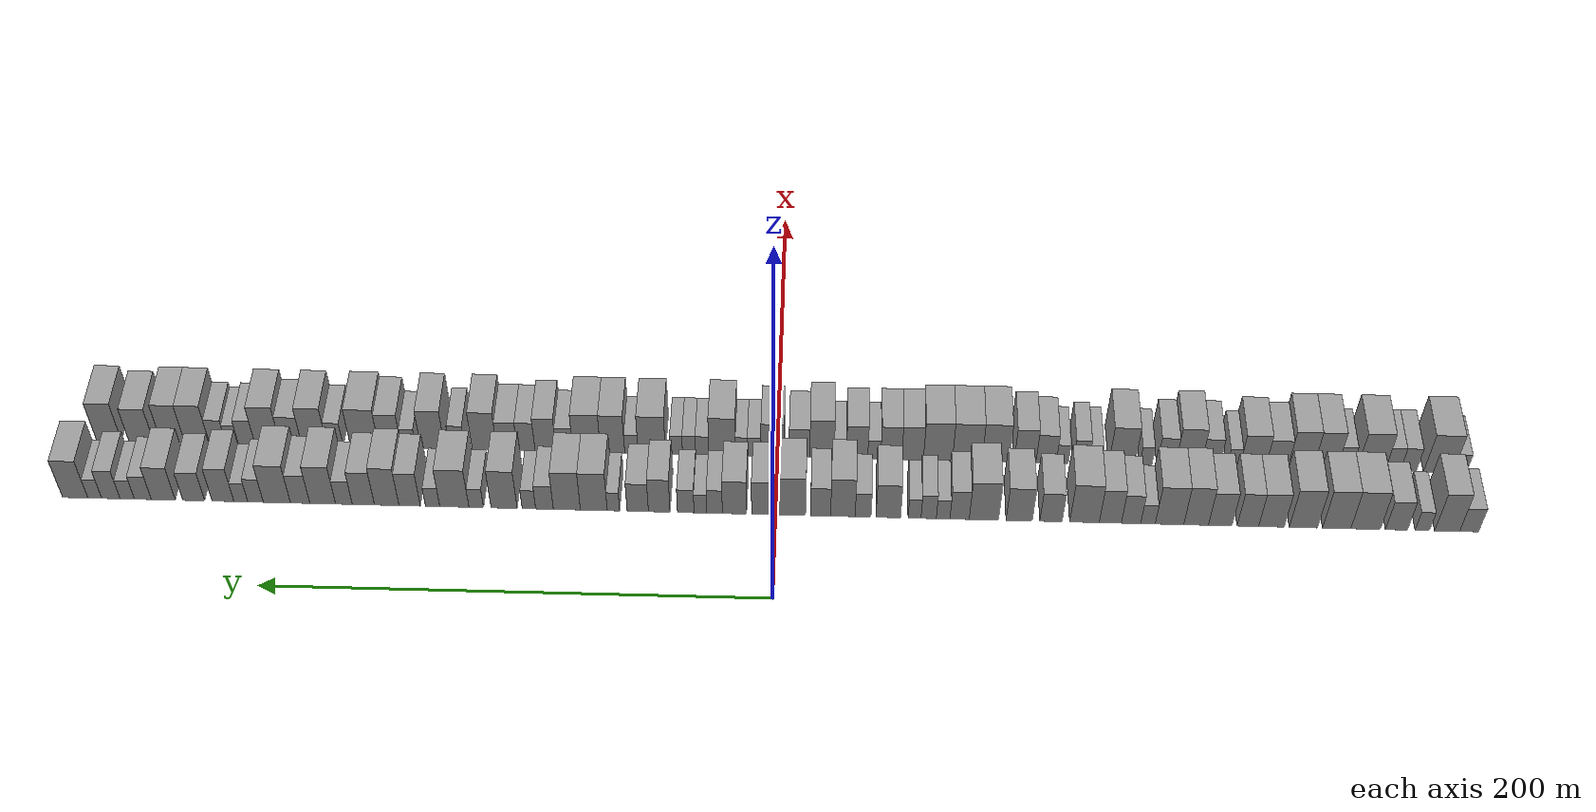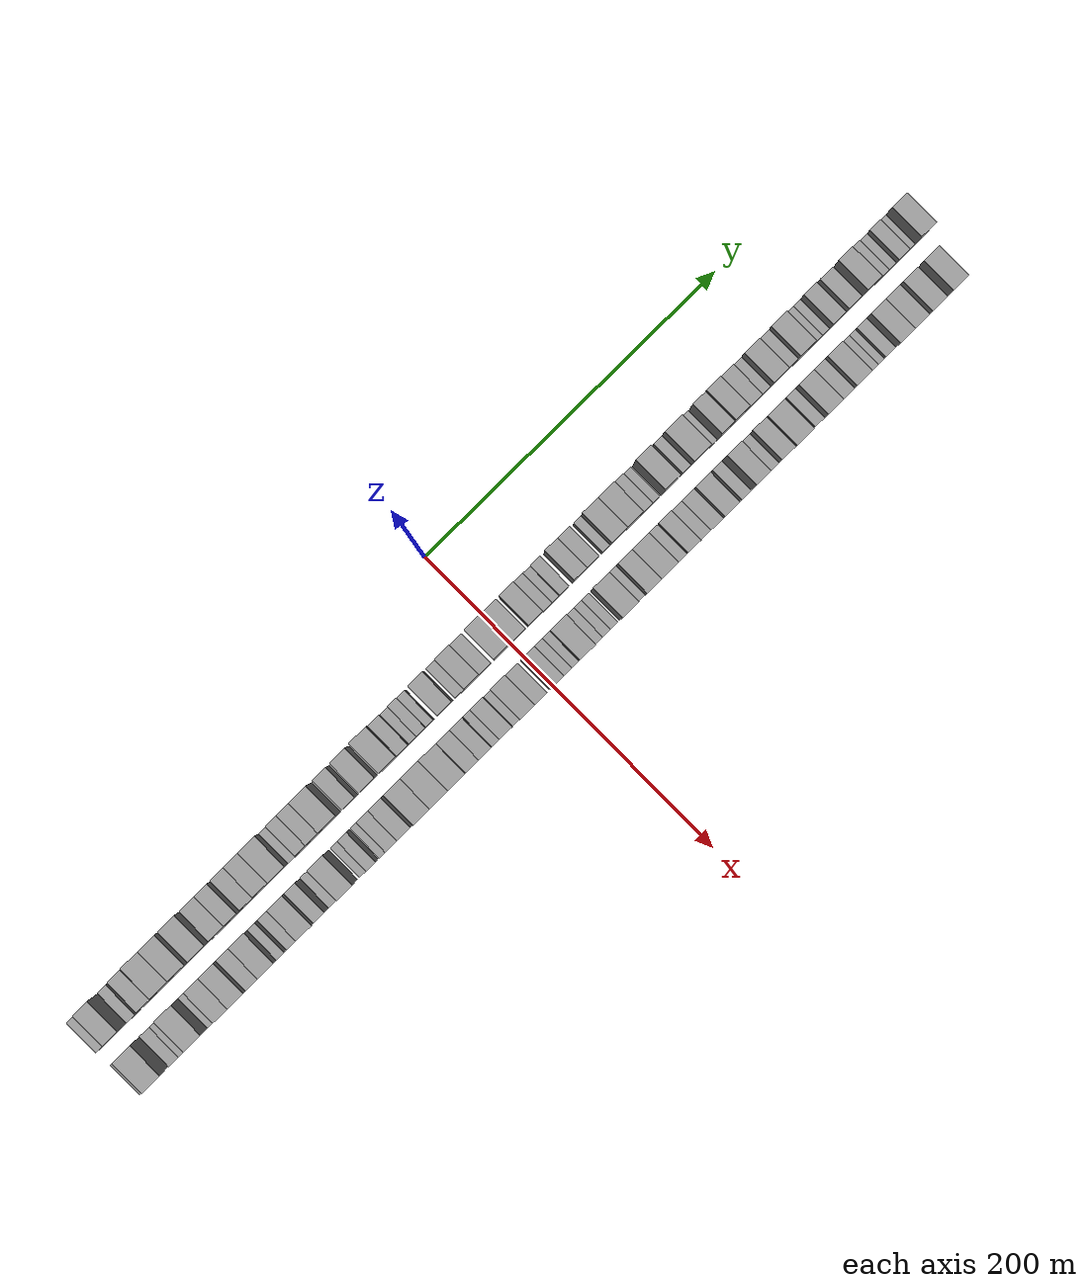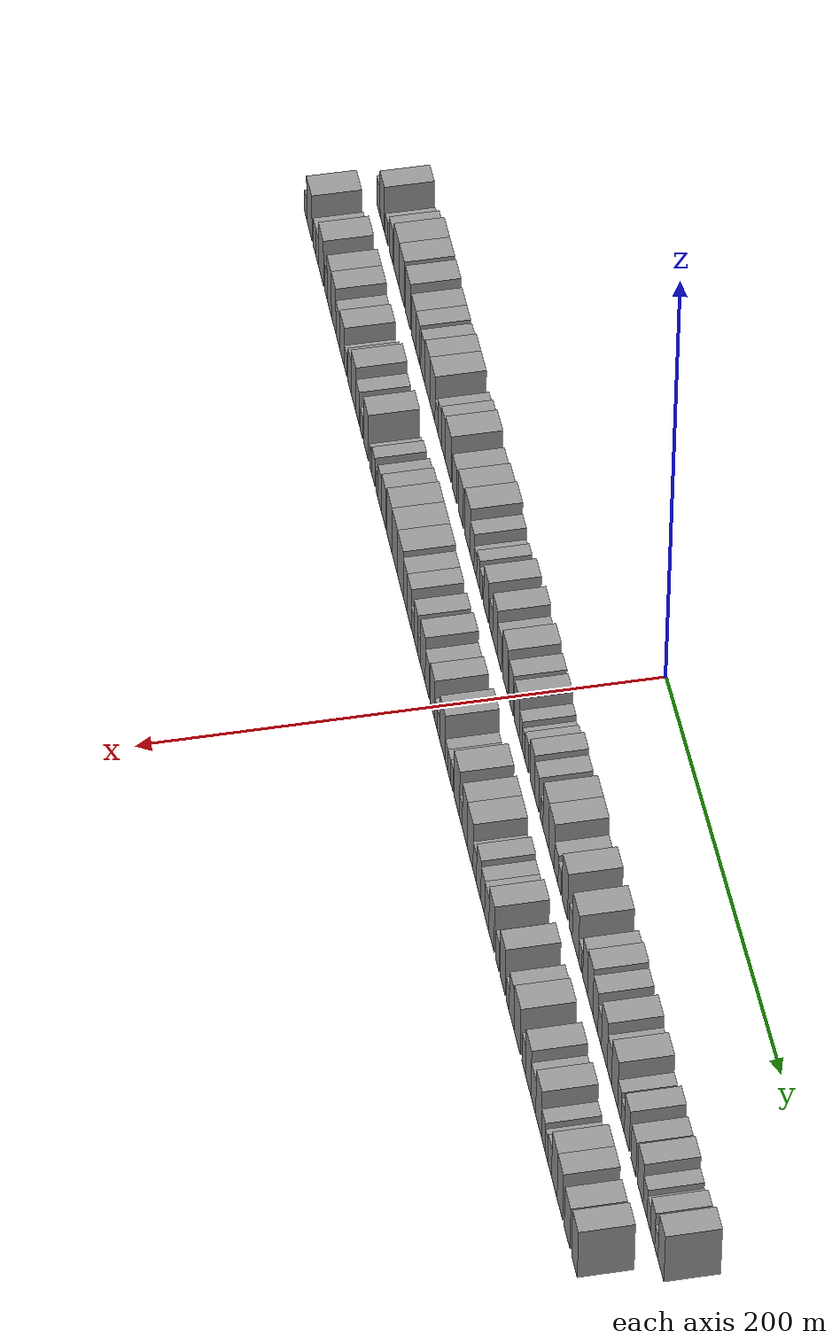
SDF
<sdf version="1.6">
 <world name="default">
  <scene>
   <sky><clouds><speed>12</speed></clouds></sky>
   <ambient>0.4 0.4 0.4 1</ambient>
   <background>0.7 0.7 0.7 1</background>
   <shadows>1</shadows>
  </scene>
  <gravity>0 0 -9.8066</gravity>
  <magnetic_field>6e-06 2.3e-05 -4.2e-05</magnetic_field>
  <physics default="0" name="default_physics" type="ode">
   <ode>
    <solver>
     <type>quick</type>
     <iters>10</iters>
     <sor>1.0</sor>
     <use_dynamic_moi_rescaling>0</use_dynamic_moi_rescaling>
    </solver>
    <constraints>
     <cfm>0</cfm>
     <erp>0.2</erp>
     <contact_max_correcting_vel>100</contact_max_correcting_vel>
     <contact_surface_layer>0.001</contact_surface_layer>
    </constraints>
   </ode>
   <max_step_size>0.004</max_step_size>
   <real_time_factor>1</real_time_factor>
   <real_time_update_rate>250</real_time_update_rate>
  </physics>
  <light name="sun" type="directional">
   <pose>0 0 10 0 0 0</pose>
   <diffuse>0.8 0.8 0.8 1</diffuse>
   <specular>0.2 0.2 0.2 1</specular>
   <attenuation>
    <range>1000</range>
    <constant>0.9</constant>
    <linear>0.01</linear>
    <quadratic>0.001</quadratic>
   </attenuation>
   <direction>-0.5 0.1 -0.9</direction>
  </light>
  <model name="building_1">
   <static>1</static>
   <pose>50.0000 -274.2800 0 0.000000 0.000000 0.000000</pose>
   <link name="link">
    <pose>0 0 7.50 0 0 0</pose>
    <collision name="collision"><geometry><box><size>20.0000 7.4400 15.0000</size></box></geometry></collision>
    <visual name="visual">
     <cast_shadows>0</cast_shadows>
     <geometry><box><size>20.0000 7.4400 15.0000</size></box></geometry>
     <material>
      <script>
       <uri>model://grey_wall/materials/scripts</uri>
       <uri>model://grey_wall/materials/textures</uri>
       <name>vrc/grey_wall</name>
      </script>
     </material>
    </visual>
   </link>
  </model>
  <model name="building_2">
   <static>1</static>
   <pose>50.0000 -265.6306 0 0.000000 0.000000 0.000000</pose>
   <link name="link">
    <pose>0 0 12.00 0 0 0</pose>
    <collision name="collision"><geometry><box><size>20.0000 9.8587 24.0000</size></box></geometry></collision>
    <visual name="visual">
     <cast_shadows>0</cast_shadows>
     <geometry><box><size>20.0000 9.8587 24.0000</size></box></geometry>
     <material>
      <script>
       <uri>model://grey_wall/materials/scripts</uri>
       <uri>model://grey_wall/materials/textures</uri>
       <name>vrc/grey_wall</name>
      </script>
     </material>
    </visual>
   </link>
  </model>
  <model name="building_3">
   <static>1</static>
   <pose>50.0000 -255.8644 0 0.000000 0.000000 0.000000</pose>
   <link name="link">
    <pose>0 0 6.00 0 0 0</pose>
    <collision name="collision"><geometry><box><size>20.0000 5.6739 12.0000</size></box></geometry></collision>
    <visual name="visual">
     <cast_shadows>0</cast_shadows>
     <geometry><box><size>20.0000 5.6739 12.0000</size></box></geometry>
     <material>
      <script>
       <uri>model://grey_wall/materials/scripts</uri>
       <uri>model://grey_wall/materials/textures</uri>
       <name>vrc/grey_wall</name>
      </script>
     </material>
    </visual>
   </link>
  </model>
  <model name="building_4">
   <static>1</static>
   <pose>50.0000 -245.6716 0 0.000000 0.000000 0.000000</pose>
   <link name="link">
    <pose>0 0 9.00 0 0 0</pose>
    <collision name="collision"><geometry><box><size>20.0000 8.7116 18.0000</size></box></geometry></collision>
    <visual name="visual">
     <cast_shadows>0</cast_shadows>
     <geometry><box><size>20.0000 8.7116 18.0000</size></box></geometry>
     <material>
      <script>
       <uri>model://grey_wall/materials/scripts</uri>
       <uri>model://grey_wall/materials/textures</uri>
       <name>vrc/grey_wall</name>
      </script>
     </material>
    </visual>
   </link>
  </model>
  <model name="building_5">
   <static>1</static>
   <pose>50.0000 -233.5031 0 0.000000 0.000000 0.000000</pose>
   <link name="link">
    <pose>0 0 12.00 0 0 0</pose>
    <collision name="collision"><geometry><box><size>20.0000 11.6254 24.0000</size></box></geometry></collision>
    <visual name="visual">
     <cast_shadows>0</cast_shadows>
     <geometry><box><size>20.0000 11.6254 24.0000</size></box></geometry>
     <material>
      <script>
       <uri>model://grey_wall/materials/scripts</uri>
       <uri>model://grey_wall/materials/textures</uri>
       <name>vrc/grey_wall</name>
      </script>
     </material>
    </visual>
   </link>
  </model>
  <model name="building_6">
   <static>1</static>
   <pose>50.0000 -222.1084 0 0.000000 0.000000 0.000000</pose>
   <link name="link">
    <pose>0 0 12.00 0 0 0</pose>
    <collision name="collision"><geometry><box><size>20.0000 11.1640 24.0000</size></box></geometry></collision>
    <visual name="visual">
     <cast_shadows>0</cast_shadows>
     <geometry><box><size>20.0000 11.1640 24.0000</size></box></geometry>
     <material>
      <script>
       <uri>model://grey_wall/materials/scripts</uri>
       <uri>model://grey_wall/materials/textures</uri>
       <name>vrc/grey_wall</name>
      </script>
     </material>
    </visual>
   </link>
  </model>
  <model name="building_7">
   <static>1</static>
   <pose>50.0000 -208.9661 0 0.000000 0.000000 0.000000</pose>
   <link name="link">
    <pose>0 0 12.00 0 0 0</pose>
    <collision name="collision"><geometry><box><size>20.0000 11.1205 24.0000</size></box></geometry></collision>
    <visual name="visual">
     <cast_shadows>0</cast_shadows>
     <geometry><box><size>20.0000 11.1205 24.0000</size></box></geometry>
     <material>
      <script>
       <uri>model://grey_wall/materials/scripts</uri>
       <uri>model://grey_wall/materials/textures</uri>
       <name>vrc/grey_wall</name>
      </script>
     </material>
    </visual>
   </link>
  </model>
  <model name="building_8">
   <static>1</static>
   <pose>50.0000 -196.3599 0 0.000000 0.000000 0.000000</pose>
   <link name="link">
    <pose>0 0 10.50 0 0 0</pose>
    <collision name="collision"><geometry><box><size>20.0000 10.0919 21.0000</size></box></geometry></collision>
    <visual name="visual">
     <cast_shadows>0</cast_shadows>
     <geometry><box><size>20.0000 10.0919 21.0000</size></box></geometry>
     <material>
      <script>
       <uri>model://grey_wall/materials/scripts</uri>
       <uri>model://grey_wall/materials/textures</uri>
       <name>vrc/grey_wall</name>
      </script>
     </material>
    </visual>
   </link>
  </model>
  <model name="building_9">
   <static>1</static>
   <pose>50.0000 -187.0492 0 0.000000 0.000000 0.000000</pose>
   <link name="link">
    <pose>0 0 10.50 0 0 0</pose>
    <collision name="collision"><geometry><box><size>20.0000 8.5296 21.0000</size></box></geometry></collision>
    <visual name="visual">
     <cast_shadows>0</cast_shadows>
     <geometry><box><size>20.0000 8.5296 21.0000</size></box></geometry>
     <material>
      <script>
       <uri>model://grey_wall/materials/scripts</uri>
       <uri>model://grey_wall/materials/textures</uri>
       <name>vrc/grey_wall</name>
      </script>
     </material>
    </visual>
   </link>
  </model>
  <model name="building_10">
   <static>1</static>
   <pose>50.0000 -176.1202 0 0.000000 0.000000 0.000000</pose>
   <link name="link">
    <pose>0 0 10.50 0 0 0</pose>
    <collision name="collision"><geometry><box><size>20.0000 9.3284 21.0000</size></box></geometry></collision>
    <visual name="visual">
     <cast_shadows>0</cast_shadows>
     <geometry><box><size>20.0000 9.3284 21.0000</size></box></geometry>
     <material>
      <script>
       <uri>model://grey_wall/materials/scripts</uri>
       <uri>model://grey_wall/materials/textures</uri>
       <name>vrc/grey_wall</name>
      </script>
     </material>
    </visual>
   </link>
  </model>
  <model name="building_11">
   <static>1</static>
   <pose>50.0000 -166.5818 0 0.000000 0.000000 0.000000</pose>
   <link name="link">
    <pose>0 0 12.00 0 0 0</pose>
    <collision name="collision"><geometry><box><size>20.0000 9.7484 24.0000</size></box></geometry></collision>
    <visual name="visual">
     <cast_shadows>0</cast_shadows>
     <geometry><box><size>20.0000 9.7484 24.0000</size></box></geometry>
     <material>
      <script>
       <uri>model://grey_wall/materials/scripts</uri>
       <uri>model://grey_wall/materials/textures</uri>
       <name>vrc/grey_wall</name>
      </script>
     </material>
    </visual>
   </link>
  </model>
  <model name="building_12">
   <static>1</static>
   <pose>50.0000 -156.0734 0 0.000000 0.000000 0.000000</pose>
   <link name="link">
    <pose>0 0 12.00 0 0 0</pose>
    <collision name="collision"><geometry><box><size>20.0000 11.2684 24.0000</size></box></geometry></collision>
    <visual name="visual">
     <cast_shadows>0</cast_shadows>
     <geometry><box><size>20.0000 11.2684 24.0000</size></box></geometry>
     <material>
      <script>
       <uri>model://grey_wall/materials/scripts</uri>
       <uri>model://grey_wall/materials/textures</uri>
       <name>vrc/grey_wall</name>
      </script>
     </material>
    </visual>
   </link>
  </model>
  <model name="building_13">
   <static>1</static>
   <pose>50.0000 -147.5744 0 0.000000 0.000000 0.000000</pose>
   <link name="link">
    <pose>0 0 6.00 0 0 0</pose>
    <collision name="collision"><geometry><box><size>20.0000 5.7296 12.0000</size></box></geometry></collision>
    <visual name="visual">
     <cast_shadows>0</cast_shadows>
     <geometry><box><size>20.0000 5.7296 12.0000</size></box></geometry>
     <material>
      <script>
       <uri>model://grey_wall/materials/scripts</uri>
       <uri>model://grey_wall/materials/textures</uri>
       <name>vrc/grey_wall</name>
      </script>
     </material>
    </visual>
   </link>
  </model>
  <model name="building_14">
   <static>1</static>
   <pose>50.0000 -140.8800 0 0.000000 0.000000 0.000000</pose>
   <link name="link">
    <pose>0 0 9.00 0 0 0</pose>
    <collision name="collision"><geometry><box><size>20.0000 7.6592 18.0000</size></box></geometry></collision>
    <visual name="visual">
     <cast_shadows>0</cast_shadows>
     <geometry><box><size>20.0000 7.6592 18.0000</size></box></geometry>
     <material>
      <script>
       <uri>model://grey_wall/materials/scripts</uri>
       <uri>model://grey_wall/materials/textures</uri>
       <name>vrc/grey_wall</name>
      </script>
     </material>
    </visual>
   </link>
  </model>
  <model name="building_15">
   <static>1</static>
   <pose>50.0000 -132.6836 0 0.000000 0.000000 0.000000</pose>
   <link name="link">
    <pose>0 0 10.50 0 0 0</pose>
    <collision name="collision"><geometry><box><size>20.0000 8.7337 21.0000</size></box></geometry></collision>
    <visual name="visual">
     <cast_shadows>0</cast_shadows>
     <geometry><box><size>20.0000 8.7337 21.0000</size></box></geometry>
     <material>
      <script>
       <uri>model://grey_wall/materials/scripts</uri>
       <uri>model://grey_wall/materials/textures</uri>
       <name>vrc/grey_wall</name>
      </script>
     </material>
    </visual>
   </link>
  </model>
  <model name="building_16">
   <static>1</static>
   <pose>50.0000 -122.4694 0 0.000000 0.000000 0.000000</pose>
   <link name="link">
    <pose>0 0 12.00 0 0 0</pose>
    <collision name="collision"><geometry><box><size>20.0000 11.6947 24.0000</size></box></geometry></collision>
    <visual name="visual">
     <cast_shadows>0</cast_shadows>
     <geometry><box><size>20.0000 11.6947 24.0000</size></box></geometry>
     <material>
      <script>
       <uri>model://grey_wall/materials/scripts</uri>
       <uri>model://grey_wall/materials/textures</uri>
       <name>vrc/grey_wall</name>
      </script>
     </material>
    </visual>
   </link>
  </model>
  <model name="building_17">
   <static>1</static>
   <pose>50.0000 -109.2025 0 0.000000 0.000000 0.000000</pose>
   <link name="link">
    <pose>0 0 9.00 0 0 0</pose>
    <collision name="collision"><geometry><box><size>20.0000 8.8392 18.0000</size></box></geometry></collision>
    <visual name="visual">
     <cast_shadows>0</cast_shadows>
     <geometry><box><size>20.0000 8.8392 18.0000</size></box></geometry>
     <material>
      <script>
       <uri>model://grey_wall/materials/scripts</uri>
       <uri>model://grey_wall/materials/textures</uri>
       <name>vrc/grey_wall</name>
      </script>
     </material>
    </visual>
   </link>
  </model>
  <model name="building_18">
   <static>1</static>
   <pose>50.0000 -96.5926 0 0.000000 0.000000 0.000000</pose>
   <link name="link">
    <pose>0 0 10.50 0 0 0</pose>
    <collision name="collision"><geometry><box><size>20.0000 10.3805 21.0000</size></box></geometry></collision>
    <visual name="visual">
     <cast_shadows>0</cast_shadows>
     <geometry><box><size>20.0000 10.3805 21.0000</size></box></geometry>
     <material>
      <script>
       <uri>model://grey_wall/materials/scripts</uri>
       <uri>model://grey_wall/materials/textures</uri>
       <name>vrc/grey_wall</name>
      </script>
     </material>
    </visual>
   </link>
  </model>
  <model name="building_19">
   <static>1</static>
   <pose>50.0000 -82.6011 0 0.000000 0.000000 0.000000</pose>
   <link name="link">
    <pose>0 0 12.00 0 0 0</pose>
    <collision name="collision"><geometry><box><size>20.0000 11.6026 24.0000</size></box></geometry></collision>
    <visual name="visual">
     <cast_shadows>0</cast_shadows>
     <geometry><box><size>20.0000 11.6026 24.0000</size></box></geometry>
     <material>
      <script>
       <uri>model://grey_wall/materials/scripts</uri>
       <uri>model://grey_wall/materials/textures</uri>
       <name>vrc/grey_wall</name>
      </script>
     </material>
    </visual>
   </link>
  </model>
  <model name="building_20">
   <static>1</static>
   <pose>50.0000 -72.9751 0 0.000000 0.000000 0.000000</pose>
   <link name="link">
    <pose>0 0 9.00 0 0 0</pose>
    <collision name="collision"><geometry><box><size>20.0000 7.6494 18.0000</size></box></geometry></collision>
    <visual name="visual">
     <cast_shadows>0</cast_shadows>
     <geometry><box><size>20.0000 7.6494 18.0000</size></box></geometry>
     <material>
      <script>
       <uri>model://grey_wall/materials/scripts</uri>
       <uri>model://grey_wall/materials/textures</uri>
       <name>vrc/grey_wall</name>
      </script>
     </material>
    </visual>
   </link>
  </model>
  <model name="building_21">
   <static>1</static>
   <pose>50.0000 -66.4450 0 0.000000 0.000000 0.000000</pose>
   <link name="link">
    <pose>0 0 6.00 0 0 0</pose>
    <collision name="collision"><geometry><box><size>20.0000 5.4107 12.0000</size></box></geometry></collision>
    <visual name="visual">
     <cast_shadows>0</cast_shadows>
     <geometry><box><size>20.0000 5.4107 12.0000</size></box></geometry>
     <material>
      <script>
       <uri>model://grey_wall/materials/scripts</uri>
       <uri>model://grey_wall/materials/textures</uri>
       <name>vrc/grey_wall</name>
      </script>
     </material>
    </visual>
   </link>
  </model>
  <model name="building_22">
   <static>1</static>
   <pose>50.0000 -60.7023 0 0.000000 0.000000 0.000000</pose>
   <link name="link">
    <pose>0 0 7.50 0 0 0</pose>
    <collision name="collision"><geometry><box><size>20.0000 6.0748 15.0000</size></box></geometry></collision>
    <visual name="visual">
     <cast_shadows>0</cast_shadows>
     <geometry><box><size>20.0000 6.0748 15.0000</size></box></geometry>
     <material>
      <script>
       <uri>model://grey_wall/materials/scripts</uri>
       <uri>model://grey_wall/materials/textures</uri>
       <name>vrc/grey_wall</name>
      </script>
     </material>
    </visual>
   </link>
  </model>
  <model name="building_23">
   <static>1</static>
   <pose>50.0000 -55.1028 0 0.000000 0.000000 0.000000</pose>
   <link name="link">
    <pose>0 0 6.00 0 0 0</pose>
    <collision name="collision"><geometry><box><size>20.0000 5.1241 12.0000</size></box></geometry></collision>
    <visual name="visual">
     <cast_shadows>0</cast_shadows>
     <geometry><box><size>20.0000 5.1241 12.0000</size></box></geometry>
     <material>
      <script>
       <uri>model://grey_wall/materials/scripts</uri>
       <uri>model://grey_wall/materials/textures</uri>
       <name>vrc/grey_wall</name>
      </script>
     </material>
    </visual>
   </link>
  </model>
  <model name="building_24">
   <static>1</static>
   <pose>50.0000 -44.6592 0 0.000000 0.000000 0.000000</pose>
   <link name="link">
    <pose>0 0 10.50 0 0 0</pose>
    <collision name="collision"><geometry><box><size>20.0000 9.7632 21.0000</size></box></geometry></collision>
    <visual name="visual">
     <cast_shadows>0</cast_shadows>
     <geometry><box><size>20.0000 9.7632 21.0000</size></box></geometry>
     <material>
      <script>
       <uri>model://grey_wall/materials/scripts</uri>
       <uri>model://grey_wall/materials/textures</uri>
       <name>vrc/grey_wall</name>
      </script>
     </material>
    </visual>
   </link>
  </model>
  <model name="building_25">
   <static>1</static>
   <pose>50.0000 -34.6333 0 0.000000 0.000000 0.000000</pose>
   <link name="link">
    <pose>0 0 7.50 0 0 0</pose>
    <collision name="collision"><geometry><box><size>20.0000 6.2885 15.0000</size></box></geometry></collision>
    <visual name="visual">
     <cast_shadows>0</cast_shadows>
     <geometry><box><size>20.0000 6.2885 15.0000</size></box></geometry>
     <material>
      <script>
       <uri>model://grey_wall/materials/scripts</uri>
       <uri>model://grey_wall/materials/textures</uri>
       <name>vrc/grey_wall</name>
      </script>
     </material>
    </visual>
   </link>
  </model>
  <model name="building_26">
   <static>1</static>
   <pose>50.0000 -26.6093 0 0.000000 0.000000 0.000000</pose>
   <link name="link">
    <pose>0 0 12.00 0 0 0</pose>
    <collision name="collision"><geometry><box><size>20.0000 9.7597 24.0000</size></box></geometry></collision>
    <visual name="visual">
     <cast_shadows>0</cast_shadows>
     <geometry><box><size>20.0000 9.7597 24.0000</size></box></geometry>
     <material>
      <script>
       <uri>model://grey_wall/materials/scripts</uri>
       <uri>model://grey_wall/materials/textures</uri>
       <name>vrc/grey_wall</name>
      </script>
     </material>
    </visual>
   </link>
  </model>
  <model name="building_27">
   <static>1</static>
   <pose>50.0000 -17.7537 0 0.000000 0.000000 0.000000</pose>
   <link name="link">
    <pose>0 0 9.00 0 0 0</pose>
    <collision name="collision"><geometry><box><size>20.0000 7.9515 18.0000</size></box></geometry></collision>
    <visual name="visual">
     <cast_shadows>0</cast_shadows>
     <geometry><box><size>20.0000 7.9515 18.0000</size></box></geometry>
     <material>
      <script>
       <uri>model://grey_wall/materials/scripts</uri>
       <uri>model://grey_wall/materials/textures</uri>
       <name>vrc/grey_wall</name>
      </script>
     </material>
    </visual>
   </link>
  </model>
  <model name="building_28">
   <static>1</static>
   <pose>50.0000 -6.4030 0 0.000000 0.000000 0.000000</pose>
   <link name="link">
    <pose>0 0 12.00 0 0 0</pose>
    <collision name="collision"><geometry><box><size>20.0000 10.7500 24.0000</size></box></geometry></collision>
    <visual name="visual">
     <cast_shadows>0</cast_shadows>
     <geometry><box><size>20.0000 10.7500 24.0000</size></box></geometry>
     <material>
      <script>
       <uri>model://grey_wall/materials/scripts</uri>
       <uri>model://grey_wall/materials/textures</uri>
       <name>vrc/grey_wall</name>
      </script>
     </material>
    </visual>
   </link>
  </model>
  <model name="building_29">
   <static>1</static>
   <pose>50.0000 5.3258 0 0.000000 0.000000 0.000000</pose>
   <link name="link">
    <pose>0 0 10.50 0 0 0</pose>
    <collision name="collision"><geometry><box><size>20.0000 8.7075 21.0000</size></box></geometry></collision>
    <visual name="visual">
     <cast_shadows>0</cast_shadows>
     <geometry><box><size>20.0000 8.7075 21.0000</size></box></geometry>
     <material>
      <script>
       <uri>model://grey_wall/materials/scripts</uri>
       <uri>model://grey_wall/materials/textures</uri>
       <name>vrc/grey_wall</name>
      </script>
     </material>
    </visual>
   </link>
  </model>
  <model name="building_30">
   <static>1</static>
   <pose>50.0000 16.5006 0 0.000000 0.000000 0.000000</pose>
   <link name="link">
    <pose>0 0 10.50 0 0 0</pose>
    <collision name="collision"><geometry><box><size>20.0000 9.6423 21.0000</size></box></geometry></collision>
    <visual name="visual">
     <cast_shadows>0</cast_shadows>
     <geometry><box><size>20.0000 9.6423 21.0000</size></box></geometry>
     <material>
      <script>
       <uri>model://grey_wall/materials/scripts</uri>
       <uri>model://grey_wall/materials/textures</uri>
       <name>vrc/grey_wall</name>
      </script>
     </material>
    </visual>
   </link>
  </model>
  <model name="building_31">
   <static>1</static>
   <pose>50.0000 24.4151 0 0.000000 0.000000 0.000000</pose>
   <link name="link">
    <pose>0 0 7.50 0 0 0</pose>
    <collision name="collision"><geometry><box><size>20.0000 6.1867 15.0000</size></box></geometry></collision>
    <visual name="visual">
     <cast_shadows>0</cast_shadows>
     <geometry><box><size>20.0000 6.1867 15.0000</size></box></geometry>
     <material>
      <script>
       <uri>model://grey_wall/materials/scripts</uri>
       <uri>model://grey_wall/materials/textures</uri>
       <name>vrc/grey_wall</name>
      </script>
     </material>
    </visual>
   </link>
  </model>
  <model name="building_32">
   <static>1</static>
   <pose>50.0000 30.0523 0 0.000000 0.000000 0.000000</pose>
   <link name="link">
    <pose>0 0 6.00 0 0 0</pose>
    <collision name="collision"><geometry><box><size>20.0000 5.0875 12.0000</size></box></geometry></collision>
    <visual name="visual">
     <cast_shadows>0</cast_shadows>
     <geometry><box><size>20.0000 5.0875 12.0000</size></box></geometry>
     <material>
      <script>
       <uri>model://grey_wall/materials/scripts</uri>
       <uri>model://grey_wall/materials/textures</uri>
       <name>vrc/grey_wall</name>
      </script>
     </material>
    </visual>
   </link>
  </model>
  <model name="building_33">
   <static>1</static>
   <pose>50.0000 35.8845 0 0.000000 0.000000 0.000000</pose>
   <link name="link">
    <pose>0 0 7.50 0 0 0</pose>
    <collision name="collision"><geometry><box><size>20.0000 6.5770 15.0000</size></box></geometry></collision>
    <visual name="visual">
     <cast_shadows>0</cast_shadows>
     <geometry><box><size>20.0000 6.5770 15.0000</size></box></geometry>
     <material>
      <script>
       <uri>model://grey_wall/materials/scripts</uri>
       <uri>model://grey_wall/materials/textures</uri>
       <name>vrc/grey_wall</name>
      </script>
     </material>
    </visual>
   </link>
  </model>
  <model name="building_34">
   <static>1</static>
   <pose>50.0000 46.4833 0 0.000000 0.000000 0.000000</pose>
   <link name="link">
    <pose>0 0 10.50 0 0 0</pose>
    <collision name="collision"><geometry><box><size>20.0000 8.6205 21.0000</size></box></geometry></collision>
    <visual name="visual">
     <cast_shadows>0</cast_shadows>
     <geometry><box><size>20.0000 8.6205 21.0000</size></box></geometry>
     <material>
      <script>
       <uri>model://grey_wall/materials/scripts</uri>
       <uri>model://grey_wall/materials/textures</uri>
       <name>vrc/grey_wall</name>
      </script>
     </material>
    </visual>
   </link>
  </model>
  <model name="building_35">
   <static>1</static>
   <pose>50.0000 55.0244 0 0.000000 0.000000 0.000000</pose>
   <link name="link">
    <pose>0 0 9.00 0 0 0</pose>
    <collision name="collision"><geometry><box><size>20.0000 8.4618 18.0000</size></box></geometry></collision>
    <visual name="visual">
     <cast_shadows>0</cast_shadows>
     <geometry><box><size>20.0000 8.4618 18.0000</size></box></geometry>
     <material>
      <script>
       <uri>model://grey_wall/materials/scripts</uri>
       <uri>model://grey_wall/materials/textures</uri>
       <name>vrc/grey_wall</name>
      </script>
     </material>
    </visual>
   </link>
  </model>
  <model name="building_36">
   <static>1</static>
   <pose>50.0000 64.7247 0 0.000000 0.000000 0.000000</pose>
   <link name="link">
    <pose>0 0 6.00 0 0 0</pose>
    <collision name="collision"><geometry><box><size>20.0000 4.9388 12.0000</size></box></geometry></collision>
    <visual name="visual">
     <cast_shadows>0</cast_shadows>
     <geometry><box><size>20.0000 4.9388 12.0000</size></box></geometry>
     <material>
      <script>
       <uri>model://grey_wall/materials/scripts</uri>
       <uri>model://grey_wall/materials/textures</uri>
       <name>vrc/grey_wall</name>
      </script>
     </material>
    </visual>
   </link>
  </model>
  <model name="building_37">
   <static>1</static>
   <pose>50.0000 72.5590 0 0.000000 0.000000 0.000000</pose>
   <link name="link">
    <pose>0 0 12.00 0 0 0</pose>
    <collision name="collision"><geometry><box><size>20.0000 10.7297 24.0000</size></box></geometry></collision>
    <visual name="visual">
     <cast_shadows>0</cast_shadows>
     <geometry><box><size>20.0000 10.7297 24.0000</size></box></geometry>
     <material>
      <script>
       <uri>model://grey_wall/materials/scripts</uri>
       <uri>model://grey_wall/materials/textures</uri>
       <name>vrc/grey_wall</name>
      </script>
     </material>
    </visual>
   </link>
  </model>
  <model name="building_38">
   <static>1</static>
   <pose>50.0000 83.3200 0 0.000000 0.000000 0.000000</pose>
   <link name="link">
    <pose>0 0 12.00 0 0 0</pose>
    <collision name="collision"><geometry><box><size>20.0000 10.7925 24.0000</size></box></geometry></collision>
    <visual name="visual">
     <cast_shadows>0</cast_shadows>
     <geometry><box><size>20.0000 10.7925 24.0000</size></box></geometry>
     <material>
      <script>
       <uri>model://grey_wall/materials/scripts</uri>
       <uri>model://grey_wall/materials/textures</uri>
       <name>vrc/grey_wall</name>
      </script>
     </material>
    </visual>
   </link>
  </model>
  <model name="building_39">
   <static>1</static>
   <pose>50.0000 92.2625 0 0.000000 0.000000 0.000000</pose>
   <link name="link">
    <pose>0 0 7.50 0 0 0</pose>
    <collision name="collision"><geometry><box><size>20.0000 7.0925 15.0000</size></box></geometry></collision>
    <visual name="visual">
     <cast_shadows>0</cast_shadows>
     <geometry><box><size>20.0000 7.0925 15.0000</size></box></geometry>
     <material>
      <script>
       <uri>model://grey_wall/materials/scripts</uri>
       <uri>model://grey_wall/materials/textures</uri>
       <name>vrc/grey_wall</name>
      </script>
     </material>
    </visual>
   </link>
  </model>
  <model name="building_40">
   <static>1</static>
   <pose>50.0000 98.4907 0 0.000000 0.000000 0.000000</pose>
   <link name="link">
    <pose>0 0 6.00 0 0 0</pose>
    <collision name="collision"><geometry><box><size>20.0000 5.3638 12.0000</size></box></geometry></collision>
    <visual name="visual">
     <cast_shadows>0</cast_shadows>
     <geometry><box><size>20.0000 5.3638 12.0000</size></box></geometry>
     <material>
      <script>
       <uri>model://grey_wall/materials/scripts</uri>
       <uri>model://grey_wall/materials/textures</uri>
       <name>vrc/grey_wall</name>
      </script>
     </material>
    </visual>
   </link>
  </model>
  <model name="building_41">
   <static>1</static>
   <pose>50.0000 108.3969 0 0.000000 0.000000 0.000000</pose>
   <link name="link">
    <pose>0 0 12.00 0 0 0</pose>
    <collision name="collision"><geometry><box><size>20.0000 10.4485 24.0000</size></box></geometry></collision>
    <visual name="visual">
     <cast_shadows>0</cast_shadows>
     <geometry><box><size>20.0000 10.4485 24.0000</size></box></geometry>
     <material>
      <script>
       <uri>model://grey_wall/materials/scripts</uri>
       <uri>model://grey_wall/materials/textures</uri>
       <name>vrc/grey_wall</name>
      </script>
     </material>
    </visual>
   </link>
  </model>
  <model name="building_42">
   <static>1</static>
   <pose>50.0000 119.5557 0 0.000000 0.000000 0.000000</pose>
   <link name="link">
    <pose>0 0 6.00 0 0 0</pose>
    <collision name="collision"><geometry><box><size>20.0000 5.8690 12.0000</size></box></geometry></collision>
    <visual name="visual">
     <cast_shadows>0</cast_shadows>
     <geometry><box><size>20.0000 5.8690 12.0000</size></box></geometry>
     <material>
      <script>
       <uri>model://grey_wall/materials/scripts</uri>
       <uri>model://grey_wall/materials/textures</uri>
       <name>vrc/grey_wall</name>
      </script>
     </material>
    </visual>
   </link>
  </model>
  <model name="building_43">
   <static>1</static>
   <pose>50.0000 128.3248 0 0.000000 0.000000 0.000000</pose>
   <link name="link">
    <pose>0 0 12.00 0 0 0</pose>
    <collision name="collision"><geometry><box><size>20.0000 11.6693 24.0000</size></box></geometry></collision>
    <visual name="visual">
     <cast_shadows>0</cast_shadows>
     <geometry><box><size>20.0000 11.6693 24.0000</size></box></geometry>
     <material>
      <script>
       <uri>model://grey_wall/materials/scripts</uri>
       <uri>model://grey_wall/materials/textures</uri>
       <name>vrc/grey_wall</name>
      </script>
     </material>
    </visual>
   </link>
  </model>
  <model name="building_44">
   <static>1</static>
   <pose>50.0000 137.0263 0 0.000000 0.000000 0.000000</pose>
   <link name="link">
    <pose>0 0 6.00 0 0 0</pose>
    <collision name="collision"><geometry><box><size>20.0000 5.7337 12.0000</size></box></geometry></collision>
    <visual name="visual">
     <cast_shadows>0</cast_shadows>
     <geometry><box><size>20.0000 5.7337 12.0000</size></box></geometry>
     <material>
      <script>
       <uri>model://grey_wall/materials/scripts</uri>
       <uri>model://grey_wall/materials/textures</uri>
       <name>vrc/grey_wall</name>
      </script>
     </material>
    </visual>
   </link>
  </model>
  <model name="building_45">
   <static>1</static>
   <pose>50.0000 146.1741 0 0.000000 0.000000 0.000000</pose>
   <link name="link">
    <pose>0 0 10.50 0 0 0</pose>
    <collision name="collision"><geometry><box><size>20.0000 8.5618 21.0000</size></box></geometry></collision>
    <visual name="visual">
     <cast_shadows>0</cast_shadows>
     <geometry><box><size>20.0000 8.5618 21.0000</size></box></geometry>
     <material>
      <script>
       <uri>model://grey_wall/materials/scripts</uri>
       <uri>model://grey_wall/materials/textures</uri>
       <name>vrc/grey_wall</name>
      </script>
     </material>
    </visual>
   </link>
  </model>
  <model name="building_46">
   <static>1</static>
   <pose>50.0000 155.3698 0 0.000000 0.000000 0.000000</pose>
   <link name="link">
    <pose>0 0 12.00 0 0 0</pose>
    <collision name="collision"><geometry><box><size>20.0000 9.8296 24.0000</size></box></geometry></collision>
    <visual name="visual">
     <cast_shadows>0</cast_shadows>
     <geometry><box><size>20.0000 9.8296 24.0000</size></box></geometry>
     <material>
      <script>
       <uri>model://grey_wall/materials/scripts</uri>
       <uri>model://grey_wall/materials/textures</uri>
       <name>vrc/grey_wall</name>
      </script>
     </material>
    </visual>
   </link>
  </model>
  <model name="building_47">
   <static>1</static>
   <pose>50.0000 164.7303 0 0.000000 0.000000 0.000000</pose>
   <link name="link">
    <pose>0 0 10.50 0 0 0</pose>
    <collision name="collision"><geometry><box><size>20.0000 8.8915 21.0000</size></box></geometry></collision>
    <visual name="visual">
     <cast_shadows>0</cast_shadows>
     <geometry><box><size>20.0000 8.8915 21.0000</size></box></geometry>
     <material>
      <script>
       <uri>model://grey_wall/materials/scripts</uri>
       <uri>model://grey_wall/materials/textures</uri>
       <name>vrc/grey_wall</name>
      </script>
     </material>
    </visual>
   </link>
  </model>
  <model name="building_48">
   <static>1</static>
   <pose>50.0000 172.5086 0 0.000000 0.000000 0.000000</pose>
   <link name="link">
    <pose>0 0 7.50 0 0 0</pose>
    <collision name="collision"><geometry><box><size>20.0000 6.6652 15.0000</size></box></geometry></collision>
    <visual name="visual">
     <cast_shadows>0</cast_shadows>
     <geometry><box><size>20.0000 6.6652 15.0000</size></box></geometry>
     <material>
      <script>
       <uri>model://grey_wall/materials/scripts</uri>
       <uri>model://grey_wall/materials/textures</uri>
       <name>vrc/grey_wall</name>
      </script>
     </material>
    </visual>
   </link>
  </model>
  <model name="building_49">
   <static>1</static>
   <pose>50.0000 181.0192 0 0.000000 0.000000 0.000000</pose>
   <link name="link">
    <pose>0 0 12.00 0 0 0</pose>
    <collision name="collision"><geometry><box><size>20.0000 10.3559 24.0000</size></box></geometry></collision>
    <visual name="visual">
     <cast_shadows>0</cast_shadows>
     <geometry><box><size>20.0000 10.3559 24.0000</size></box></geometry>
     <material>
      <script>
       <uri>model://grey_wall/materials/scripts</uri>
       <uri>model://grey_wall/materials/textures</uri>
       <name>vrc/grey_wall</name>
      </script>
     </material>
    </visual>
   </link>
  </model>
  <model name="building_50">
   <static>1</static>
   <pose>50.0000 190.0867 0 0.000000 0.000000 0.000000</pose>
   <link name="link">
    <pose>0 0 9.00 0 0 0</pose>
    <collision name="collision"><geometry><box><size>20.0000 7.7792 18.0000</size></box></geometry></collision>
    <visual name="visual">
     <cast_shadows>0</cast_shadows>
     <geometry><box><size>20.0000 7.7792 18.0000</size></box></geometry>
     <material>
      <script>
       <uri>model://grey_wall/materials/scripts</uri>
       <uri>model://grey_wall/materials/textures</uri>
       <name>vrc/grey_wall</name>
      </script>
     </material>
    </visual>
   </link>
  </model>
  <model name="building_51">
   <static>1</static>
   <pose>50.0000 199.4191 0 0.000000 0.000000 0.000000</pose>
   <link name="link">
    <pose>0 0 12.00 0 0 0</pose>
    <collision name="collision"><geometry><box><size>20.0000 10.8854 24.0000</size></box></geometry></collision>
    <visual name="visual">
     <cast_shadows>0</cast_shadows>
     <geometry><box><size>20.0000 10.8854 24.0000</size></box></geometry>
     <material>
      <script>
       <uri>model://grey_wall/materials/scripts</uri>
       <uri>model://grey_wall/materials/textures</uri>
       <name>vrc/grey_wall</name>
      </script>
     </material>
    </visual>
   </link>
  </model>
  <model name="building_52">
   <static>1</static>
   <pose>50.0000 207.9827 0 0.000000 0.000000 0.000000</pose>
   <link name="link">
    <pose>0 0 7.50 0 0 0</pose>
    <collision name="collision"><geometry><box><size>20.0000 6.2417 15.0000</size></box></geometry></collision>
    <visual name="visual">
     <cast_shadows>0</cast_shadows>
     <geometry><box><size>20.0000 6.2417 15.0000</size></box></geometry>
     <material>
      <script>
       <uri>model://grey_wall/materials/scripts</uri>
       <uri>model://grey_wall/materials/textures</uri>
       <name>vrc/grey_wall</name>
      </script>
     </material>
    </visual>
   </link>
  </model>
  <model name="building_53">
   <static>1</static>
   <pose>50.0000 213.8942 0 0.000000 0.000000 0.000000</pose>
   <link name="link">
    <pose>0 0 6.00 0 0 0</pose>
    <collision name="collision"><geometry><box><size>20.0000 5.5813 12.0000</size></box></geometry></collision>
    <visual name="visual">
     <cast_shadows>0</cast_shadows>
     <geometry><box><size>20.0000 5.5813 12.0000</size></box></geometry>
     <material>
      <script>
       <uri>model://grey_wall/materials/scripts</uri>
       <uri>model://grey_wall/materials/textures</uri>
       <name>vrc/grey_wall</name>
      </script>
     </material>
    </visual>
   </link>
  </model>
  <model name="building_54">
   <static>1</static>
   <pose>50.0000 221.0543 0 0.000000 0.000000 0.000000</pose>
   <link name="link">
    <pose>0 0 10.50 0 0 0</pose>
    <collision name="collision"><geometry><box><size>20.0000 8.7389 21.0000</size></box></geometry></collision>
    <visual name="visual">
     <cast_shadows>0</cast_shadows>
     <geometry><box><size>20.0000 8.7389 21.0000</size></box></geometry>
     <material>
      <script>
       <uri>model://grey_wall/materials/scripts</uri>
       <uri>model://grey_wall/materials/textures</uri>
       <name>vrc/grey_wall</name>
      </script>
     </material>
    </visual>
   </link>
  </model>
  <model name="building_55">
   <static>1</static>
   <pose>50.0000 232.8241 0 0.000000 0.000000 0.000000</pose>
   <link name="link">
    <pose>0 0 9.00 0 0 0</pose>
    <collision name="collision"><geometry><box><size>20.0000 8.8006 18.0000</size></box></geometry></collision>
    <visual name="visual">
     <cast_shadows>0</cast_shadows>
     <geometry><box><size>20.0000 8.8006 18.0000</size></box></geometry>
     <material>
      <script>
       <uri>model://grey_wall/materials/scripts</uri>
       <uri>model://grey_wall/materials/textures</uri>
       <name>vrc/grey_wall</name>
      </script>
     </material>
    </visual>
   </link>
  </model>
  <model name="building_56">
   <static>1</static>
   <pose>50.0000 245.0541 0 0.000000 0.000000 0.000000</pose>
   <link name="link">
    <pose>0 0 10.50 0 0 0</pose>
    <collision name="collision"><geometry><box><size>20.0000 9.6595 21.0000</size></box></geometry></collision>
    <visual name="visual">
     <cast_shadows>0</cast_shadows>
     <geometry><box><size>20.0000 9.6595 21.0000</size></box></geometry>
     <material>
      <script>
       <uri>model://grey_wall/materials/scripts</uri>
       <uri>model://grey_wall/materials/textures</uri>
       <name>vrc/grey_wall</name>
      </script>
     </material>
    </visual>
   </link>
  </model>
  <model name="building_57">
   <static>1</static>
   <pose>50.0000 253.2717 0 0.000000 0.000000 0.000000</pose>
   <link name="link">
    <pose>0 0 7.50 0 0 0</pose>
    <collision name="collision"><geometry><box><size>20.0000 6.7756 15.0000</size></box></geometry></collision>
    <visual name="visual">
     <cast_shadows>0</cast_shadows>
     <geometry><box><size>20.0000 6.7756 15.0000</size></box></geometry>
     <material>
      <script>
       <uri>model://grey_wall/materials/scripts</uri>
       <uri>model://grey_wall/materials/textures</uri>
       <name>vrc/grey_wall</name>
      </script>
     </material>
    </visual>
   </link>
  </model>
  <model name="building_58">
   <static>1</static>
   <pose>50.0000 259.5477 0 0.000000 0.000000 0.000000</pose>
   <link name="link">
    <pose>0 0 6.00 0 0 0</pose>
    <collision name="collision"><geometry><box><size>20.0000 5.7763 12.0000</size></box></geometry></collision>
    <visual name="visual">
     <cast_shadows>0</cast_shadows>
     <geometry><box><size>20.0000 5.7763 12.0000</size></box></geometry>
     <material>
      <script>
       <uri>model://grey_wall/materials/scripts</uri>
       <uri>model://grey_wall/materials/textures</uri>
       <name>vrc/grey_wall</name>
      </script>
     </material>
    </visual>
   </link>
  </model>
  <model name="building_59">
   <static>1</static>
   <pose>50.0000 266.1331 0 0.000000 0.000000 0.000000</pose>
   <link name="link">
    <pose>0 0 9.00 0 0 0</pose>
    <collision name="collision"><geometry><box><size>20.0000 7.3945 18.0000</size></box></geometry></collision>
    <visual name="visual">
     <cast_shadows>0</cast_shadows>
     <geometry><box><size>20.0000 7.3945 18.0000</size></box></geometry>
     <material>
      <script>
       <uri>model://grey_wall/materials/scripts</uri>
       <uri>model://grey_wall/materials/textures</uri>
       <name>vrc/grey_wall</name>
      </script>
     </material>
    </visual>
   </link>
  </model>
  <model name="building_60">
   <static>1</static>
   <pose>50.0000 272.6167 0 0.000000 0.000000 0.000000</pose>
   <link name="link">
    <pose>0 0 6.00 0 0 0</pose>
    <collision name="collision"><geometry><box><size>20.0000 5.5727 12.0000</size></box></geometry></collision>
    <visual name="visual">
     <cast_shadows>0</cast_shadows>
     <geometry><box><size>20.0000 5.5727 12.0000</size></box></geometry>
     <material>
      <script>
       <uri>model://grey_wall/materials/scripts</uri>
       <uri>model://grey_wall/materials/textures</uri>
       <name>vrc/grey_wall</name>
      </script>
     </material>
    </visual>
   </link>
  </model>
  <model name="building_61">
   <static>1</static>
   <pose>50.0000 280.4854 0 0.000000 0.000000 0.000000</pose>
   <link name="link">
    <pose>0 0 12.00 0 0 0</pose>
    <collision name="collision"><geometry><box><size>20.0000 10.1645 24.0000</size></box></geometry></collision>
    <visual name="visual">
     <cast_shadows>0</cast_shadows>
     <geometry><box><size>20.0000 10.1645 24.0000</size></box></geometry>
     <material>
      <script>
       <uri>model://grey_wall/materials/scripts</uri>
       <uri>model://grey_wall/materials/textures</uri>
       <name>vrc/grey_wall</name>
      </script>
     </material>
    </visual>
   </link>
  </model>
  <model name="building_62">
   <static>1</static>
   <pose>79.0000 -275.3712 0 0.000000 0.000000 0.000000</pose>
   <link name="link">
    <pose>0 0 6.00 0 0 0</pose>
    <collision name="collision"><geometry><box><size>20.0000 5.2576 12.0000</size></box></geometry></collision>
    <visual name="visual">
     <cast_shadows>0</cast_shadows>
     <geometry><box><size>20.0000 5.2576 12.0000</size></box></geometry>
     <material>
      <script>
       <uri>model://grey_wall/materials/scripts</uri>
       <uri>model://grey_wall/materials/textures</uri>
       <name>vrc/grey_wall</name>
      </script>
     </material>
    </visual>
   </link>
  </model>
  <model name="building_63">
   <static>1</static>
   <pose>79.0000 -266.7910 0 0.000000 0.000000 0.000000</pose>
   <link name="link">
    <pose>0 0 12.00 0 0 0</pose>
    <collision name="collision"><geometry><box><size>20.0000 11.9027 24.0000</size></box></geometry></collision>
    <visual name="visual">
     <cast_shadows>0</cast_shadows>
     <geometry><box><size>20.0000 11.9027 24.0000</size></box></geometry>
     <material>
      <script>
       <uri>model://grey_wall/materials/scripts</uri>
       <uri>model://grey_wall/materials/textures</uri>
       <name>vrc/grey_wall</name>
      </script>
     </material>
    </visual>
   </link>
  </model>
  <model name="building_64">
   <static>1</static>
   <pose>79.0000 -254.6164 0 0.000000 0.000000 0.000000</pose>
   <link name="link">
    <pose>0 0 7.50 0 0 0</pose>
    <collision name="collision"><geometry><box><size>20.0000 6.4466 15.0000</size></box></geometry></collision>
    <visual name="visual">
     <cast_shadows>0</cast_shadows>
     <geometry><box><size>20.0000 6.4466 15.0000</size></box></geometry>
     <material>
      <script>
       <uri>model://grey_wall/materials/scripts</uri>
       <uri>model://grey_wall/materials/textures</uri>
       <name>vrc/grey_wall</name>
      </script>
     </material>
    </visual>
   </link>
  </model>
  <model name="building_65">
   <static>1</static>
   <pose>79.0000 -248.3477 0 0.000000 0.000000 0.000000</pose>
   <link name="link">
    <pose>0 0 7.50 0 0 0</pose>
    <collision name="collision"><geometry><box><size>20.0000 6.0907 15.0000</size></box></geometry></collision>
    <visual name="visual">
     <cast_shadows>0</cast_shadows>
     <geometry><box><size>20.0000 6.0907 15.0000</size></box></geometry>
     <material>
      <script>
       <uri>model://grey_wall/materials/scripts</uri>
       <uri>model://grey_wall/materials/textures</uri>
       <name>vrc/grey_wall</name>
      </script>
     </material>
    </visual>
   </link>
  </model>
  <model name="building_66">
   <static>1</static>
   <pose>79.0000 -239.6394 0 0.000000 0.000000 0.000000</pose>
   <link name="link">
    <pose>0 0 12.00 0 0 0</pose>
    <collision name="collision"><geometry><box><size>20.0000 11.3260 24.0000</size></box></geometry></collision>
    <visual name="visual">
     <cast_shadows>0</cast_shadows>
     <geometry><box><size>20.0000 11.3260 24.0000</size></box></geometry>
     <material>
      <script>
       <uri>model://grey_wall/materials/scripts</uri>
       <uri>model://grey_wall/materials/textures</uri>
       <name>vrc/grey_wall</name>
      </script>
     </material>
    </visual>
   </link>
  </model>
  <model name="building_67">
   <static>1</static>
   <pose>79.0000 -228.9631 0 0.000000 0.000000 0.000000</pose>
   <link name="link">
    <pose>0 0 7.50 0 0 0</pose>
    <collision name="collision"><geometry><box><size>20.0000 6.0266 15.0000</size></box></geometry></collision>
    <visual name="visual">
     <cast_shadows>0</cast_shadows>
     <geometry><box><size>20.0000 6.0266 15.0000</size></box></geometry>
     <material>
      <script>
       <uri>model://grey_wall/materials/scripts</uri>
       <uri>model://grey_wall/materials/textures</uri>
       <name>vrc/grey_wall</name>
      </script>
     </material>
    </visual>
   </link>
  </model>
  <model name="building_68">
   <static>1</static>
   <pose>79.0000 -221.1383 0 0.000000 0.000000 0.000000</pose>
   <link name="link">
    <pose>0 0 12.00 0 0 0</pose>
    <collision name="collision"><geometry><box><size>20.0000 9.6230 24.0000</size></box></geometry></collision>
    <visual name="visual">
     <cast_shadows>0</cast_shadows>
     <geometry><box><size>20.0000 9.6230 24.0000</size></box></geometry>
     <material>
      <script>
       <uri>model://grey_wall/materials/scripts</uri>
       <uri>model://grey_wall/materials/textures</uri>
       <name>vrc/grey_wall</name>
      </script>
     </material>
    </visual>
   </link>
  </model>
  <model name="building_69">
   <static>1</static>
   <pose>79.0000 -211.1753 0 0.000000 0.000000 0.000000</pose>
   <link name="link">
    <pose>0 0 12.00 0 0 0</pose>
    <collision name="collision"><geometry><box><size>20.0000 10.3030 24.0000</size></box></geometry></collision>
    <visual name="visual">
     <cast_shadows>0</cast_shadows>
     <geometry><box><size>20.0000 10.3030 24.0000</size></box></geometry>
     <material>
      <script>
       <uri>model://grey_wall/materials/scripts</uri>
       <uri>model://grey_wall/materials/textures</uri>
       <name>vrc/grey_wall</name>
      </script>
     </material>
    </visual>
   </link>
  </model>
  <model name="building_70">
   <static>1</static>
   <pose>79.0000 -201.5853 0 0.000000 0.000000 0.000000</pose>
   <link name="link">
    <pose>0 0 9.00 0 0 0</pose>
    <collision name="collision"><geometry><box><size>20.0000 8.8771 18.0000</size></box></geometry></collision>
    <visual name="visual">
     <cast_shadows>0</cast_shadows>
     <geometry><box><size>20.0000 8.8771 18.0000</size></box></geometry>
     <material>
      <script>
       <uri>model://grey_wall/materials/scripts</uri>
       <uri>model://grey_wall/materials/textures</uri>
       <name>vrc/grey_wall</name>
      </script>
     </material>
    </visual>
   </link>
  </model>
  <model name="building_71">
   <static>1</static>
   <pose>79.0000 -191.9220 0 0.000000 0.000000 0.000000</pose>
   <link name="link">
    <pose>0 0 10.50 0 0 0</pose>
    <collision name="collision"><geometry><box><size>20.0000 10.4494 21.0000</size></box></geometry></collision>
    <visual name="visual">
     <cast_shadows>0</cast_shadows>
     <geometry><box><size>20.0000 10.4494 21.0000</size></box></geometry>
     <material>
      <script>
       <uri>model://grey_wall/materials/scripts</uri>
       <uri>model://grey_wall/materials/textures</uri>
       <name>vrc/grey_wall</name>
      </script>
     </material>
    </visual>
   </link>
  </model>
  <model name="building_72">
   <static>1</static>
   <pose>79.0000 -184.1596 0 0.000000 0.000000 0.000000</pose>
   <link name="link">
    <pose>0 0 6.00 0 0 0</pose>
    <collision name="collision"><geometry><box><size>20.0000 5.0755 12.0000</size></box></geometry></collision>
    <visual name="visual">
     <cast_shadows>0</cast_shadows>
     <geometry><box><size>20.0000 5.0755 12.0000</size></box></geometry>
     <material>
      <script>
       <uri>model://grey_wall/materials/scripts</uri>
       <uri>model://grey_wall/materials/textures</uri>
       <name>vrc/grey_wall</name>
      </script>
     </material>
    </visual>
   </link>
  </model>
  <model name="building_73">
   <static>1</static>
   <pose>79.0000 -174.8725 0 0.000000 0.000000 0.000000</pose>
   <link name="link">
    <pose>0 0 9.00 0 0 0</pose>
    <collision name="collision"><geometry><box><size>20.0000 7.4987 18.0000</size></box></geometry></collision>
    <visual name="visual">
     <cast_shadows>0</cast_shadows>
     <geometry><box><size>20.0000 7.4987 18.0000</size></box></geometry>
     <material>
      <script>
       <uri>model://grey_wall/materials/scripts</uri>
       <uri>model://grey_wall/materials/textures</uri>
       <name>vrc/grey_wall</name>
      </script>
     </material>
    </visual>
   </link>
  </model>
  <model name="building_74">
   <static>1</static>
   <pose>79.0000 -165.9466 0 0.000000 0.000000 0.000000</pose>
   <link name="link">
    <pose>0 0 12.00 0 0 0</pose>
    <collision name="collision"><geometry><box><size>20.0000 10.3530 24.0000</size></box></geometry></collision>
    <visual name="visual">
     <cast_shadows>0</cast_shadows>
     <geometry><box><size>20.0000 10.3530 24.0000</size></box></geometry>
     <material>
      <script>
       <uri>model://grey_wall/materials/scripts</uri>
       <uri>model://grey_wall/materials/textures</uri>
       <name>vrc/grey_wall</name>
      </script>
     </material>
    </visual>
   </link>
  </model>
  <model name="building_75">
   <static>1</static>
   <pose>79.0000 -157.0801 0 0.000000 0.000000 0.000000</pose>
   <link name="link">
    <pose>0 0 9.00 0 0 0</pose>
    <collision name="collision"><geometry><box><size>20.0000 7.3802 18.0000</size></box></geometry></collision>
    <visual name="visual">
     <cast_shadows>0</cast_shadows>
     <geometry><box><size>20.0000 7.3802 18.0000</size></box></geometry>
     <material>
      <script>
       <uri>model://grey_wall/materials/scripts</uri>
       <uri>model://grey_wall/materials/textures</uri>
       <name>vrc/grey_wall</name>
      </script>
     </material>
    </visual>
   </link>
  </model>
  <model name="building_76">
   <static>1</static>
   <pose>79.0000 -148.9262 0 0.000000 0.000000 0.000000</pose>
   <link name="link">
    <pose>0 0 6.00 0 0 0</pose>
    <collision name="collision"><geometry><box><size>20.0000 4.9275 12.0000</size></box></geometry></collision>
    <visual name="visual">
     <cast_shadows>0</cast_shadows>
     <geometry><box><size>20.0000 4.9275 12.0000</size></box></geometry>
     <material>
      <script>
       <uri>model://grey_wall/materials/scripts</uri>
       <uri>model://grey_wall/materials/textures</uri>
       <name>vrc/grey_wall</name>
      </script>
     </material>
    </visual>
   </link>
  </model>
  <model name="building_77">
   <static>1</static>
   <pose>79.0000 -139.1802 0 0.000000 0.000000 0.000000</pose>
   <link name="link">
    <pose>0 0 12.00 0 0 0</pose>
    <collision name="collision"><geometry><box><size>20.0000 10.5644 24.0000</size></box></geometry></collision>
    <visual name="visual">
     <cast_shadows>0</cast_shadows>
     <geometry><box><size>20.0000 10.5644 24.0000</size></box></geometry>
     <material>
      <script>
       <uri>model://grey_wall/materials/scripts</uri>
       <uri>model://grey_wall/materials/textures</uri>
       <name>vrc/grey_wall</name>
      </script>
     </material>
    </visual>
   </link>
  </model>
  <model name="building_78">
   <static>1</static>
   <pose>79.0000 -128.4122 0 0.000000 0.000000 0.000000</pose>
   <link name="link">
    <pose>0 0 6.00 0 0 0</pose>
    <collision name="collision"><geometry><box><size>20.0000 4.9716 12.0000</size></box></geometry></collision>
    <visual name="visual">
     <cast_shadows>0</cast_shadows>
     <geometry><box><size>20.0000 4.9716 12.0000</size></box></geometry>
     <material>
      <script>
       <uri>model://grey_wall/materials/scripts</uri>
       <uri>model://grey_wall/materials/textures</uri>
       <name>vrc/grey_wall</name>
      </script>
     </material>
    </visual>
   </link>
  </model>
  <model name="building_79">
   <static>1</static>
   <pose>79.0000 -122.7783 0 0.000000 0.000000 0.000000</pose>
   <link name="link">
    <pose>0 0 7.50 0 0 0</pose>
    <collision name="collision"><geometry><box><size>20.0000 6.2963 15.0000</size></box></geometry></collision>
    <visual name="visual">
     <cast_shadows>0</cast_shadows>
     <geometry><box><size>20.0000 6.2963 15.0000</size></box></geometry>
     <material>
      <script>
       <uri>model://grey_wall/materials/scripts</uri>
       <uri>model://grey_wall/materials/textures</uri>
       <name>vrc/grey_wall</name>
      </script>
     </material>
    </visual>
   </link>
  </model>
  <model name="building_80">
   <static>1</static>
   <pose>79.0000 -115.1872 0 0.000000 0.000000 0.000000</pose>
   <link name="link">
    <pose>0 0 6.00 0 0 0</pose>
    <collision name="collision"><geometry><box><size>20.0000 4.8861 12.0000</size></box></geometry></collision>
    <visual name="visual">
     <cast_shadows>0</cast_shadows>
     <geometry><box><size>20.0000 4.8861 12.0000</size></box></geometry>
     <material>
      <script>
       <uri>model://grey_wall/materials/scripts</uri>
       <uri>model://grey_wall/materials/textures</uri>
       <name>vrc/grey_wall</name>
      </script>
     </material>
    </visual>
   </link>
  </model>
  <model name="building_81">
   <static>1</static>
   <pose>79.0000 -108.6356 0 0.000000 0.000000 0.000000</pose>
   <link name="link">
    <pose>0 0 9.00 0 0 0</pose>
    <collision name="collision"><geometry><box><size>20.0000 8.2170 18.0000</size></box></geometry></collision>
    <visual name="visual">
     <cast_shadows>0</cast_shadows>
     <geometry><box><size>20.0000 8.2170 18.0000</size></box></geometry>
     <material>
      <script>
       <uri>model://grey_wall/materials/scripts</uri>
       <uri>model://grey_wall/materials/textures</uri>
       <name>vrc/grey_wall</name>
      </script>
     </material>
    </visual>
   </link>
  </model>
  <model name="building_82">
   <static>1</static>
   <pose>79.0000 -100.1014 0 0.000000 0.000000 0.000000</pose>
   <link name="link">
    <pose>0 0 10.50 0 0 0</pose>
    <collision name="collision"><geometry><box><size>20.0000 8.8514 21.0000</size></box></geometry></collision>
    <visual name="visual">
     <cast_shadows>0</cast_shadows>
     <geometry><box><size>20.0000 8.8514 21.0000</size></box></geometry>
     <material>
      <script>
       <uri>model://grey_wall/materials/scripts</uri>
       <uri>model://grey_wall/materials/textures</uri>
       <name>vrc/grey_wall</name>
      </script>
     </material>
    </visual>
   </link>
  </model>
  <model name="building_83">
   <static>1</static>
   <pose>79.0000 -88.1874 0 0.000000 0.000000 0.000000</pose>
   <link name="link">
    <pose>0 0 12.00 0 0 0</pose>
    <collision name="collision"><geometry><box><size>20.0000 10.9766 24.0000</size></box></geometry></collision>
    <visual name="visual">
     <cast_shadows>0</cast_shadows>
     <geometry><box><size>20.0000 10.9766 24.0000</size></box></geometry>
     <material>
      <script>
       <uri>model://grey_wall/materials/scripts</uri>
       <uri>model://grey_wall/materials/textures</uri>
       <name>vrc/grey_wall</name>
      </script>
     </material>
    </visual>
   </link>
  </model>
  <model name="building_84">
   <static>1</static>
   <pose>79.0000 -76.7188 0 0.000000 0.000000 0.000000</pose>
   <link name="link">
    <pose>0 0 12.00 0 0 0</pose>
    <collision name="collision"><geometry><box><size>20.0000 11.9605 24.0000</size></box></geometry></collision>
    <visual name="visual">
     <cast_shadows>0</cast_shadows>
     <geometry><box><size>20.0000 11.9605 24.0000</size></box></geometry>
     <material>
      <script>
       <uri>model://grey_wall/materials/scripts</uri>
       <uri>model://grey_wall/materials/textures</uri>
       <name>vrc/grey_wall</name>
      </script>
     </material>
    </visual>
   </link>
  </model>
  <model name="building_85">
   <static>1</static>
   <pose>79.0000 -64.8581 0 0.000000 0.000000 0.000000</pose>
   <link name="link">
    <pose>0 0 12.00 0 0 0</pose>
    <collision name="collision"><geometry><box><size>20.0000 11.7610 24.0000</size></box></geometry></collision>
    <visual name="visual">
     <cast_shadows>0</cast_shadows>
     <geometry><box><size>20.0000 11.7610 24.0000</size></box></geometry>
     <material>
      <script>
       <uri>model://grey_wall/materials/scripts</uri>
       <uri>model://grey_wall/materials/textures</uri>
       <name>vrc/grey_wall</name>
      </script>
     </material>
    </visual>
   </link>
  </model>
  <model name="building_86">
   <static>1</static>
   <pose>79.0000 -54.5589 0 0.000000 0.000000 0.000000</pose>
   <link name="link">
    <pose>0 0 10.50 0 0 0</pose>
    <collision name="collision"><geometry><box><size>20.0000 8.8374 21.0000</size></box></geometry></collision>
    <visual name="visual">
     <cast_shadows>0</cast_shadows>
     <geometry><box><size>20.0000 8.8374 21.0000</size></box></geometry>
     <material>
      <script>
       <uri>model://grey_wall/materials/scripts</uri>
       <uri>model://grey_wall/materials/textures</uri>
       <name>vrc/grey_wall</name>
      </script>
     </material>
    </visual>
   </link>
  </model>
  <model name="building_87">
   <static>1</static>
   <pose>79.0000 -45.8797 0 0.000000 0.000000 0.000000</pose>
   <link name="link">
    <pose>0 0 10.50 0 0 0</pose>
    <collision name="collision"><geometry><box><size>20.0000 8.5209 21.0000</size></box></geometry></collision>
    <visual name="visual">
     <cast_shadows>0</cast_shadows>
     <geometry><box><size>20.0000 8.5209 21.0000</size></box></geometry>
     <material>
      <script>
       <uri>model://grey_wall/materials/scripts</uri>
       <uri>model://grey_wall/materials/textures</uri>
       <name>vrc/grey_wall</name>
      </script>
     </material>
    </visual>
   </link>
  </model>
  <model name="building_88">
   <static>1</static>
   <pose>79.0000 -39.0088 0 0.000000 0.000000 0.000000</pose>
   <link name="link">
    <pose>0 0 6.00 0 0 0</pose>
    <collision name="collision"><geometry><box><size>20.0000 5.2211 12.0000</size></box></geometry></collision>
    <visual name="visual">
     <cast_shadows>0</cast_shadows>
     <geometry><box><size>20.0000 5.2211 12.0000</size></box></geometry>
     <material>
      <script>
       <uri>model://grey_wall/materials/scripts</uri>
       <uri>model://grey_wall/materials/textures</uri>
       <name>vrc/grey_wall</name>
      </script>
     </material>
    </visual>
   </link>
  </model>
  <model name="building_89">
   <static>1</static>
   <pose>79.0000 -32.0551 0 0.000000 0.000000 0.000000</pose>
   <link name="link">
    <pose>0 0 10.50 0 0 0</pose>
    <collision name="collision"><geometry><box><size>20.0000 8.6862 21.0000</size></box></geometry></collision>
    <visual name="visual">
     <cast_shadows>0</cast_shadows>
     <geometry><box><size>20.0000 8.6862 21.0000</size></box></geometry>
     <material>
      <script>
       <uri>model://grey_wall/materials/scripts</uri>
       <uri>model://grey_wall/materials/textures</uri>
       <name>vrc/grey_wall</name>
      </script>
     </material>
    </visual>
   </link>
  </model>
  <model name="building_90">
   <static>1</static>
   <pose>79.0000 -25.2470 0 0.000000 0.000000 0.000000</pose>
   <link name="link">
    <pose>0 0 6.00 0 0 0</pose>
    <collision name="collision"><geometry><box><size>20.0000 4.9300 12.0000</size></box></geometry></collision>
    <visual name="visual">
     <cast_shadows>0</cast_shadows>
     <geometry><box><size>20.0000 4.9300 12.0000</size></box></geometry>
     <material>
      <script>
       <uri>model://grey_wall/materials/scripts</uri>
       <uri>model://grey_wall/materials/textures</uri>
       <name>vrc/grey_wall</name>
      </script>
     </material>
    </visual>
   </link>
  </model>
  <model name="building_91">
   <static>1</static>
   <pose>79.0000 -17.8389 0 0.000000 0.000000 0.000000</pose>
   <link name="link">
    <pose>0 0 12.00 0 0 0</pose>
    <collision name="collision"><geometry><box><size>20.0000 9.8862 24.0000</size></box></geometry></collision>
    <visual name="visual">
     <cast_shadows>0</cast_shadows>
     <geometry><box><size>20.0000 9.8862 24.0000</size></box></geometry>
     <material>
      <script>
       <uri>model://grey_wall/materials/scripts</uri>
       <uri>model://grey_wall/materials/textures</uri>
       <name>vrc/grey_wall</name>
      </script>
     </material>
    </visual>
   </link>
  </model>
  <model name="building_92">
   <static>1</static>
   <pose>79.0000 -8.7081 0 0.000000 0.000000 0.000000</pose>
   <link name="link">
    <pose>0 0 9.00 0 0 0</pose>
    <collision name="collision"><geometry><box><size>20.0000 8.3756 18.0000</size></box></geometry></collision>
    <visual name="visual">
     <cast_shadows>0</cast_shadows>
     <geometry><box><size>20.0000 8.3756 18.0000</size></box></geometry>
     <material>
      <script>
       <uri>model://grey_wall/materials/scripts</uri>
       <uri>model://grey_wall/materials/textures</uri>
       <name>vrc/grey_wall</name>
      </script>
     </material>
    </visual>
   </link>
  </model>
  <model name="building_93">
   <static>1</static>
   <pose>79.0000 2.1678 0 0.000000 0.000000 0.000000</pose>
   <link name="link">
    <pose>0 0 10.50 0 0 0</pose>
    <collision name="collision"><geometry><box><size>20.0000 9.3761 21.0000</size></box></geometry></collision>
    <visual name="visual">
     <cast_shadows>0</cast_shadows>
     <geometry><box><size>20.0000 9.3761 21.0000</size></box></geometry>
     <material>
      <script>
       <uri>model://grey_wall/materials/scripts</uri>
       <uri>model://grey_wall/materials/textures</uri>
       <name>vrc/grey_wall</name>
      </script>
     </material>
    </visual>
   </link>
  </model>
  <model name="building_94">
   <static>1</static>
   <pose>79.0000 9.6142 0 0.000000 0.000000 0.000000</pose>
   <link name="link">
    <pose>0 0 6.00 0 0 0</pose>
    <collision name="collision"><geometry><box><size>20.0000 5.5166 12.0000</size></box></geometry></collision>
    <visual name="visual">
     <cast_shadows>0</cast_shadows>
     <geometry><box><size>20.0000 5.5166 12.0000</size></box></geometry>
     <material>
      <script>
       <uri>model://grey_wall/materials/scripts</uri>
       <uri>model://grey_wall/materials/textures</uri>
       <name>vrc/grey_wall</name>
      </script>
     </material>
    </visual>
   </link>
  </model>
  <model name="building_95">
   <static>1</static>
   <pose>79.0000 14.8140 0 0.000000 0.000000 0.000000</pose>
   <link name="link">
    <pose>0 0 6.00 0 0 0</pose>
    <collision name="collision"><geometry><box><size>20.0000 4.8831 12.0000</size></box></geometry></collision>
    <visual name="visual">
     <cast_shadows>0</cast_shadows>
     <geometry><box><size>20.0000 4.8831 12.0000</size></box></geometry>
     <material>
      <script>
       <uri>model://grey_wall/materials/scripts</uri>
       <uri>model://grey_wall/materials/textures</uri>
       <name>vrc/grey_wall</name>
      </script>
     </material>
    </visual>
   </link>
  </model>
  <model name="building_96">
   <static>1</static>
   <pose>79.0000 22.6443 0 0.000000 0.000000 0.000000</pose>
   <link name="link">
    <pose>0 0 12.00 0 0 0</pose>
    <collision name="collision"><geometry><box><size>20.0000 10.7775 24.0000</size></box></geometry></collision>
    <visual name="visual">
     <cast_shadows>0</cast_shadows>
     <geometry><box><size>20.0000 10.7775 24.0000</size></box></geometry>
     <material>
      <script>
       <uri>model://grey_wall/materials/scripts</uri>
       <uri>model://grey_wall/materials/textures</uri>
       <name>vrc/grey_wall</name>
      </script>
     </material>
    </visual>
   </link>
  </model>
  <model name="building_97">
   <static>1</static>
   <pose>79.0000 30.7441 0 0.000000 0.000000 0.000000</pose>
   <link name="link">
    <pose>0 0 6.00 0 0 0</pose>
    <collision name="collision"><geometry><box><size>20.0000 5.4222 12.0000</size></box></geometry></collision>
    <visual name="visual">
     <cast_shadows>0</cast_shadows>
     <geometry><box><size>20.0000 5.4222 12.0000</size></box></geometry>
     <material>
      <script>
       <uri>model://grey_wall/materials/scripts</uri>
       <uri>model://grey_wall/materials/textures</uri>
       <name>vrc/grey_wall</name>
      </script>
     </material>
    </visual>
   </link>
  </model>
  <model name="building_98">
   <static>1</static>
   <pose>79.0000 36.1029 0 0.000000 0.000000 0.000000</pose>
   <link name="link">
    <pose>0 0 6.00 0 0 0</pose>
    <collision name="collision"><geometry><box><size>20.0000 5.2954 12.0000</size></box></geometry></collision>
    <visual name="visual">
     <cast_shadows>0</cast_shadows>
     <geometry><box><size>20.0000 5.2954 12.0000</size></box></geometry>
     <material>
      <script>
       <uri>model://grey_wall/materials/scripts</uri>
       <uri>model://grey_wall/materials/textures</uri>
       <name>vrc/grey_wall</name>
      </script>
     </material>
    </visual>
   </link>
  </model>
  <model name="building_99">
   <static>1</static>
   <pose>79.0000 41.2283 0 0.000000 0.000000 0.000000</pose>
   <link name="link">
    <pose>0 0 6.00 0 0 0</pose>
    <collision name="collision"><geometry><box><size>20.0000 4.9553 12.0000</size></box></geometry></collision>
    <visual name="visual">
     <cast_shadows>0</cast_shadows>
     <geometry><box><size>20.0000 4.9553 12.0000</size></box></geometry>
     <material>
      <script>
       <uri>model://grey_wall/materials/scripts</uri>
       <uri>model://grey_wall/materials/textures</uri>
       <name>vrc/grey_wall</name>
      </script>
     </material>
    </visual>
   </link>
  </model>
  <model name="building_100">
   <static>1</static>
   <pose>79.0000 51.2626 0 0.000000 0.000000 0.000000</pose>
   <link name="link">
    <pose>0 0 12.00 0 0 0</pose>
    <collision name="collision"><geometry><box><size>20.0000 11.1134 24.0000</size></box></geometry></collision>
    <visual name="visual">
     <cast_shadows>0</cast_shadows>
     <geometry><box><size>20.0000 11.1134 24.0000</size></box></geometry>
     <material>
      <script>
       <uri>model://grey_wall/materials/scripts</uri>
       <uri>model://grey_wall/materials/textures</uri>
       <name>vrc/grey_wall</name>
      </script>
     </material>
    </visual>
   </link>
  </model>
  <model name="building_101">
   <static>1</static>
   <pose>79.0000 59.5426 0 0.000000 0.000000 0.000000</pose>
   <link name="link">
    <pose>0 0 6.00 0 0 0</pose>
    <collision name="collision"><geometry><box><size>20.0000 5.4466 12.0000</size></box></geometry></collision>
    <visual name="visual">
     <cast_shadows>0</cast_shadows>
     <geometry><box><size>20.0000 5.4466 12.0000</size></box></geometry>
     <material>
      <script>
       <uri>model://grey_wall/materials/scripts</uri>
       <uri>model://grey_wall/materials/textures</uri>
       <name>vrc/grey_wall</name>
      </script>
     </material>
    </visual>
   </link>
  </model>
  <model name="building_102">
   <static>1</static>
   <pose>79.0000 67.1863 0 0.000000 0.000000 0.000000</pose>
   <link name="link">
    <pose>0 0 12.00 0 0 0</pose>
    <collision name="collision"><geometry><box><size>20.0000 9.8408 24.0000</size></box></geometry></collision>
    <visual name="visual">
     <cast_shadows>0</cast_shadows>
     <geometry><box><size>20.0000 9.8408 24.0000</size></box></geometry>
     <material>
      <script>
       <uri>model://grey_wall/materials/scripts</uri>
       <uri>model://grey_wall/materials/textures</uri>
       <name>vrc/grey_wall</name>
      </script>
     </material>
    </visual>
   </link>
  </model>
  <model name="building_103">
   <static>1</static>
   <pose>79.0000 77.7209 0 0.000000 0.000000 0.000000</pose>
   <link name="link">
    <pose>0 0 12.00 0 0 0</pose>
    <collision name="collision"><geometry><box><size>20.0000 11.2283 24.0000</size></box></geometry></collision>
    <visual name="visual">
     <cast_shadows>0</cast_shadows>
     <geometry><box><size>20.0000 11.2283 24.0000</size></box></geometry>
     <material>
      <script>
       <uri>model://grey_wall/materials/scripts</uri>
       <uri>model://grey_wall/materials/textures</uri>
       <name>vrc/grey_wall</name>
      </script>
     </material>
    </visual>
   </link>
  </model>
  <model name="building_104">
   <static>1</static>
   <pose>79.0000 86.7648 0 0.000000 0.000000 0.000000</pose>
   <link name="link">
    <pose>0 0 7.50 0 0 0</pose>
    <collision name="collision"><geometry><box><size>20.0000 6.8595 15.0000</size></box></geometry></collision>
    <visual name="visual">
     <cast_shadows>0</cast_shadows>
     <geometry><box><size>20.0000 6.8595 15.0000</size></box></geometry>
     <material>
      <script>
       <uri>model://grey_wall/materials/scripts</uri>
       <uri>model://grey_wall/materials/textures</uri>
       <name>vrc/grey_wall</name>
      </script>
     </material>
    </visual>
   </link>
  </model>
  <model name="building_105">
   <static>1</static>
   <pose>79.0000 94.4989 0 0.000000 0.000000 0.000000</pose>
   <link name="link">
    <pose>0 0 10.50 0 0 0</pose>
    <collision name="collision"><geometry><box><size>20.0000 8.6088 21.0000</size></box></geometry></collision>
    <visual name="visual">
     <cast_shadows>0</cast_shadows>
     <geometry><box><size>20.0000 8.6088 21.0000</size></box></geometry>
     <material>
      <script>
       <uri>model://grey_wall/materials/scripts</uri>
       <uri>model://grey_wall/materials/textures</uri>
       <name>vrc/grey_wall</name>
      </script>
     </material>
    </visual>
   </link>
  </model>
  <model name="building_106">
   <static>1</static>
   <pose>79.0000 102.4062 0 0.000000 0.000000 0.000000</pose>
   <link name="link">
    <pose>0 0 9.00 0 0 0</pose>
    <collision name="collision"><geometry><box><size>20.0000 7.2058 18.0000</size></box></geometry></collision>
    <visual name="visual">
     <cast_shadows>0</cast_shadows>
     <geometry><box><size>20.0000 7.2058 18.0000</size></box></geometry>
     <material>
      <script>
       <uri>model://grey_wall/materials/scripts</uri>
       <uri>model://grey_wall/materials/textures</uri>
       <name>vrc/grey_wall</name>
      </script>
     </material>
    </visual>
   </link>
  </model>
  <model name="building_107">
   <static>1</static>
   <pose>79.0000 110.1682 0 0.000000 0.000000 0.000000</pose>
   <link name="link">
    <pose>0 0 9.00 0 0 0</pose>
    <collision name="collision"><geometry><box><size>20.0000 8.3181 18.0000</size></box></geometry></collision>
    <visual name="visual">
     <cast_shadows>0</cast_shadows>
     <geometry><box><size>20.0000 8.3181 18.0000</size></box></geometry>
     <material>
      <script>
       <uri>model://grey_wall/materials/scripts</uri>
       <uri>model://grey_wall/materials/textures</uri>
       <name>vrc/grey_wall</name>
      </script>
     </material>
    </visual>
   </link>
  </model>
  <model name="building_108">
   <static>1</static>
   <pose>79.0000 119.3735 0 0.000000 0.000000 0.000000</pose>
   <link name="link">
    <pose>0 0 12.00 0 0 0</pose>
    <collision name="collision"><geometry><box><size>20.0000 10.0926 24.0000</size></box></geometry></collision>
    <visual name="visual">
     <cast_shadows>0</cast_shadows>
     <geometry><box><size>20.0000 10.0926 24.0000</size></box></geometry>
     <material>
      <script>
       <uri>model://grey_wall/materials/scripts</uri>
       <uri>model://grey_wall/materials/textures</uri>
       <name>vrc/grey_wall</name>
      </script>
     </material>
    </visual>
   </link>
  </model>
  <model name="building_109">
   <static>1</static>
   <pose>79.0000 130.5140 0 0.000000 0.000000 0.000000</pose>
   <link name="link">
    <pose>0 0 7.50 0 0 0</pose>
    <collision name="collision"><geometry><box><size>20.0000 6.1885 15.0000</size></box></geometry></collision>
    <visual name="visual">
     <cast_shadows>0</cast_shadows>
     <geometry><box><size>20.0000 6.1885 15.0000</size></box></geometry>
     <material>
      <script>
       <uri>model://grey_wall/materials/scripts</uri>
       <uri>model://grey_wall/materials/textures</uri>
       <name>vrc/grey_wall</name>
      </script>
     </material>
    </visual>
   </link>
  </model>
  <model name="building_110">
   <static>1</static>
   <pose>79.0000 140.5212 0 0.000000 0.000000 0.000000</pose>
   <link name="link">
    <pose>0 0 12.00 0 0 0</pose>
    <collision name="collision"><geometry><box><size>20.0000 9.8259 24.0000</size></box></geometry></collision>
    <visual name="visual">
     <cast_shadows>0</cast_shadows>
     <geometry><box><size>20.0000 9.8259 24.0000</size></box></geometry>
     <material>
      <script>
       <uri>model://grey_wall/materials/scripts</uri>
       <uri>model://grey_wall/materials/textures</uri>
       <name>vrc/grey_wall</name>
      </script>
     </material>
    </visual>
   </link>
  </model>
  <model name="building_111">
   <static>1</static>
   <pose>79.0000 150.3769 0 0.000000 0.000000 0.000000</pose>
   <link name="link">
    <pose>0 0 6.00 0 0 0</pose>
    <collision name="collision"><geometry><box><size>20.0000 5.8856 12.0000</size></box></geometry></collision>
    <visual name="visual">
     <cast_shadows>0</cast_shadows>
     <geometry><box><size>20.0000 5.8856 12.0000</size></box></geometry>
     <material>
      <script>
       <uri>model://grey_wall/materials/scripts</uri>
       <uri>model://grey_wall/materials/textures</uri>
       <name>vrc/grey_wall</name>
      </script>
     </material>
    </visual>
   </link>
  </model>
  <model name="building_112">
   <static>1</static>
   <pose>79.0000 157.9287 0 0.000000 0.000000 0.000000</pose>
   <link name="link">
    <pose>0 0 10.50 0 0 0</pose>
    <collision name="collision"><geometry><box><size>20.0000 9.2180 21.0000</size></box></geometry></collision>
    <visual name="visual">
     <cast_shadows>0</cast_shadows>
     <geometry><box><size>20.0000 9.2180 21.0000</size></box></geometry>
     <material>
      <script>
       <uri>model://grey_wall/materials/scripts</uri>
       <uri>model://grey_wall/materials/textures</uri>
       <name>vrc/grey_wall</name>
      </script>
     </material>
    </visual>
   </link>
  </model>
  <model name="building_113">
   <static>1</static>
   <pose>79.0000 168.3629 0 0.000000 0.000000 0.000000</pose>
   <link name="link">
    <pose>0 0 12.00 0 0 0</pose>
    <collision name="collision"><geometry><box><size>20.0000 11.6503 24.0000</size></box></geometry></collision>
    <visual name="visual">
     <cast_shadows>0</cast_shadows>
     <geometry><box><size>20.0000 11.6503 24.0000</size></box></geometry>
     <material>
      <script>
       <uri>model://grey_wall/materials/scripts</uri>
       <uri>model://grey_wall/materials/textures</uri>
       <name>vrc/grey_wall</name>
      </script>
     </material>
    </visual>
   </link>
  </model>
  <model name="building_114">
   <static>1</static>
   <pose>79.0000 180.5038 0 0.000000 0.000000 0.000000</pose>
   <link name="link">
    <pose>0 0 7.50 0 0 0</pose>
    <collision name="collision"><geometry><box><size>20.0000 6.6314 15.0000</size></box></geometry></collision>
    <visual name="visual">
     <cast_shadows>0</cast_shadows>
     <geometry><box><size>20.0000 6.6314 15.0000</size></box></geometry>
     <material>
      <script>
       <uri>model://grey_wall/materials/scripts</uri>
       <uri>model://grey_wall/materials/textures</uri>
       <name>vrc/grey_wall</name>
      </script>
     </material>
    </visual>
   </link>
  </model>
  <model name="building_115">
   <static>1</static>
   <pose>79.0000 188.9808 0 0.000000 0.000000 0.000000</pose>
   <link name="link">
    <pose>0 0 12.00 0 0 0</pose>
    <collision name="collision"><geometry><box><size>20.0000 10.3225 24.0000</size></box></geometry></collision>
    <visual name="visual">
     <cast_shadows>0</cast_shadows>
     <geometry><box><size>20.0000 10.3225 24.0000</size></box></geometry>
     <material>
      <script>
       <uri>model://grey_wall/materials/scripts</uri>
       <uri>model://grey_wall/materials/textures</uri>
       <name>vrc/grey_wall</name>
      </script>
     </material>
    </visual>
   </link>
  </model>
  <model name="building_116">
   <static>1</static>
   <pose>79.0000 198.5715 0 0.000000 0.000000 0.000000</pose>
   <link name="link">
    <pose>0 0 9.00 0 0 0</pose>
    <collision name="collision"><geometry><box><size>20.0000 8.8590 18.0000</size></box></geometry></collision>
    <visual name="visual">
     <cast_shadows>0</cast_shadows>
     <geometry><box><size>20.0000 8.8590 18.0000</size></box></geometry>
     <material>
      <script>
       <uri>model://grey_wall/materials/scripts</uri>
       <uri>model://grey_wall/materials/textures</uri>
       <name>vrc/grey_wall</name>
      </script>
     </material>
    </visual>
   </link>
  </model>
  <model name="building_117">
   <static>1</static>
   <pose>79.0000 208.1903 0 0.000000 0.000000 0.000000</pose>
   <link name="link">
    <pose>0 0 12.00 0 0 0</pose>
    <collision name="collision"><geometry><box><size>20.0000 10.3785 24.0000</size></box></geometry></collision>
    <visual name="visual">
     <cast_shadows>0</cast_shadows>
     <geometry><box><size>20.0000 10.3785 24.0000</size></box></geometry>
     <material>
      <script>
       <uri>model://grey_wall/materials/scripts</uri>
       <uri>model://grey_wall/materials/textures</uri>
       <name>vrc/grey_wall</name>
      </script>
     </material>
    </visual>
   </link>
  </model>
  <model name="building_118">
   <static>1</static>
   <pose>79.0000 216.7969 0 0.000000 0.000000 0.000000</pose>
   <link name="link">
    <pose>0 0 7.50 0 0 0</pose>
    <collision name="collision"><geometry><box><size>20.0000 6.8348 15.0000</size></box></geometry></collision>
    <visual name="visual">
     <cast_shadows>0</cast_shadows>
     <geometry><box><size>20.0000 6.8348 15.0000</size></box></geometry>
     <material>
      <script>
       <uri>model://grey_wall/materials/scripts</uri>
       <uri>model://grey_wall/materials/textures</uri>
       <name>vrc/grey_wall</name>
      </script>
     </material>
    </visual>
   </link>
  </model>
  <model name="building_119">
   <static>1</static>
   <pose>79.0000 222.7622 0 0.000000 0.000000 0.000000</pose>
   <link name="link">
    <pose>0 0 6.00 0 0 0</pose>
    <collision name="collision"><geometry><box><size>20.0000 5.0958 12.0000</size></box></geometry></collision>
    <visual name="visual">
     <cast_shadows>0</cast_shadows>
     <geometry><box><size>20.0000 5.0958 12.0000</size></box></geometry>
     <material>
      <script>
       <uri>model://grey_wall/materials/scripts</uri>
       <uri>model://grey_wall/materials/textures</uri>
       <name>vrc/grey_wall</name>
      </script>
     </material>
    </visual>
   </link>
  </model>
  <model name="building_120">
   <static>1</static>
   <pose>79.0000 228.6952 0 0.000000 0.000000 0.000000</pose>
   <link name="link">
    <pose>0 0 7.50 0 0 0</pose>
    <collision name="collision"><geometry><box><size>20.0000 6.7700 15.0000</size></box></geometry></collision>
    <visual name="visual">
     <cast_shadows>0</cast_shadows>
     <geometry><box><size>20.0000 6.7700 15.0000</size></box></geometry>
     <material>
      <script>
       <uri>model://grey_wall/materials/scripts</uri>
       <uri>model://grey_wall/materials/textures</uri>
       <name>vrc/grey_wall</name>
      </script>
     </material>
    </visual>
   </link>
  </model>
  <model name="building_121">
   <static>1</static>
   <pose>79.0000 237.1414 0 0.000000 0.000000 0.000000</pose>
   <link name="link">
    <pose>0 0 12.00 0 0 0</pose>
    <collision name="collision"><geometry><box><size>20.0000 10.1224 24.0000</size></box></geometry></collision>
    <visual name="visual">
     <cast_shadows>0</cast_shadows>
     <geometry><box><size>20.0000 10.1224 24.0000</size></box></geometry>
     <material>
      <script>
       <uri>model://grey_wall/materials/scripts</uri>
       <uri>model://grey_wall/materials/textures</uri>
       <name>vrc/grey_wall</name>
      </script>
     </material>
    </visual>
   </link>
  </model>
  <model name="building_122">
   <static>1</static>
   <pose>79.0000 247.0811 0 0.000000 0.000000 0.000000</pose>
   <link name="link">
    <pose>0 0 12.00 0 0 0</pose>
    <collision name="collision"><geometry><box><size>20.0000 9.7570 24.0000</size></box></geometry></collision>
    <visual name="visual">
     <cast_shadows>0</cast_shadows>
     <geometry><box><size>20.0000 9.7570 24.0000</size></box></geometry>
     <material>
      <script>
       <uri>model://grey_wall/materials/scripts</uri>
       <uri>model://grey_wall/materials/textures</uri>
       <name>vrc/grey_wall</name>
      </script>
     </material>
    </visual>
   </link>
  </model>
  <model name="building_123">
   <static>1</static>
   <pose>79.0000 260.0393 0 0.000000 0.000000 0.000000</pose>
   <link name="link">
    <pose>0 0 10.50 0 0 0</pose>
    <collision name="collision"><geometry><box><size>20.0000 10.1595 21.0000</size></box></geometry></collision>
    <visual name="visual">
     <cast_shadows>0</cast_shadows>
     <geometry><box><size>20.0000 10.1595 21.0000</size></box></geometry>
     <material>
      <script>
       <uri>model://grey_wall/materials/scripts</uri>
       <uri>model://grey_wall/materials/textures</uri>
       <name>vrc/grey_wall</name>
      </script>
     </material>
    </visual>
   </link>
  </model>
  <model name="building_124">
   <static>1</static>
   <pose>79.0000 273.2315 0 0.000000 0.000000 0.000000</pose>
   <link name="link">
    <pose>0 0 12.00 0 0 0</pose>
    <collision name="collision"><geometry><box><size>20.0000 10.2249 24.0000</size></box></geometry></collision>
    <visual name="visual">
     <cast_shadows>0</cast_shadows>
     <geometry><box><size>20.0000 10.2249 24.0000</size></box></geometry>
     <material>
      <script>
       <uri>model://grey_wall/materials/scripts</uri>
       <uri>model://grey_wall/materials/textures</uri>
       <name>vrc/grey_wall</name>
      </script>
     </material>
    </visual>
   </link>
  </model>
 </world>
</sdf>
